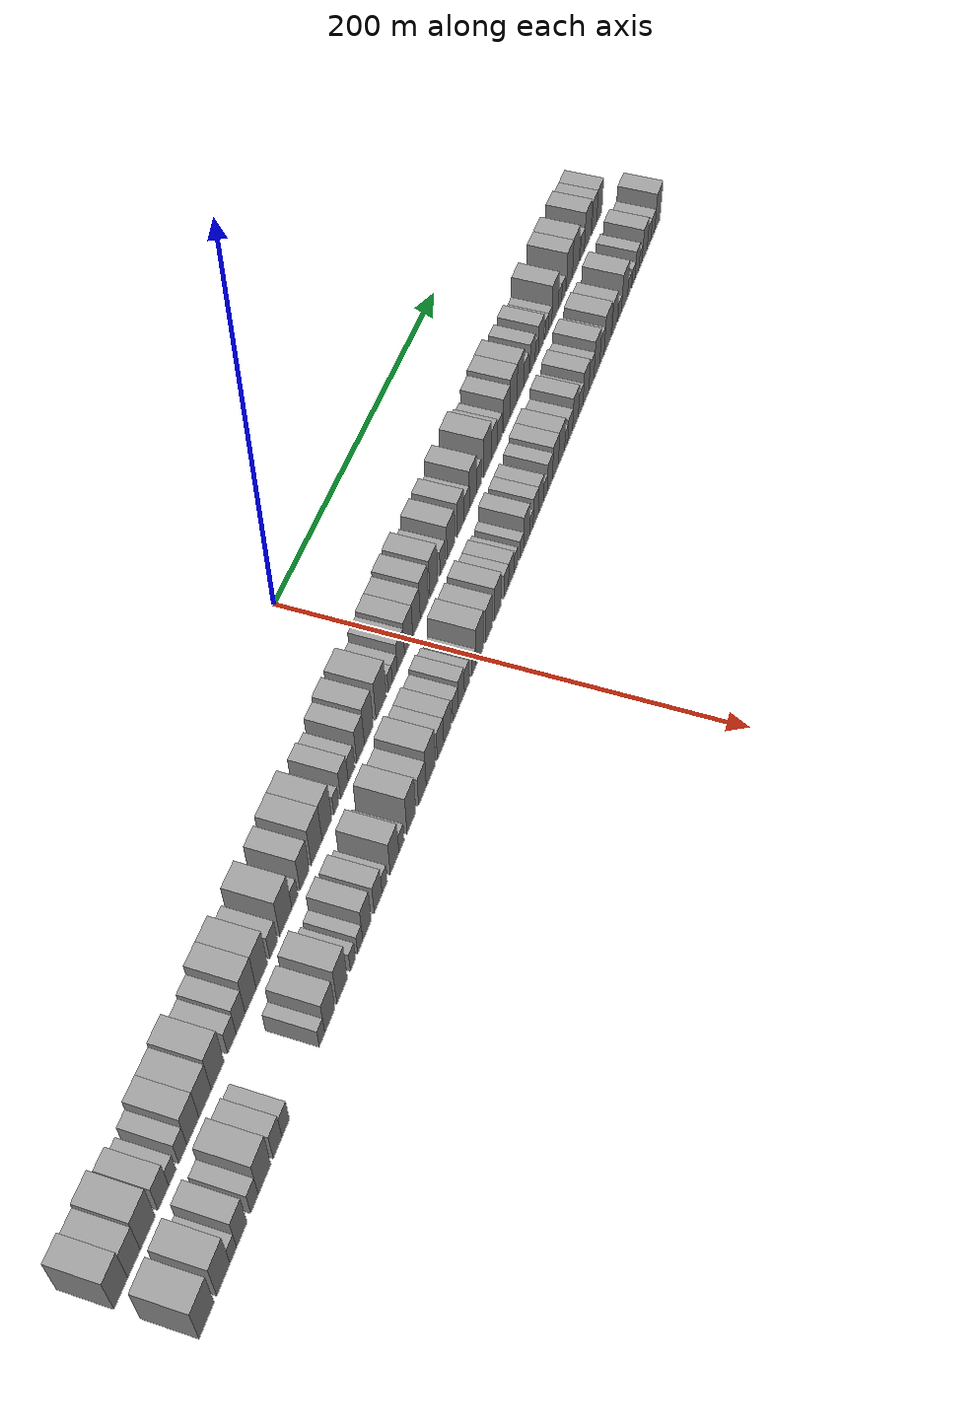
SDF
<sdf version="1.6">
 <world name="default">
  <scene>
   <sky><clouds><speed>12</speed></clouds></sky>
   <ambient>0.4 0.4 0.4 1</ambient>
   <background>0.7 0.7 0.7 1</background>
   <shadows>1</shadows>
  </scene>
  <gravity>0 0 -9.8066</gravity>
  <magnetic_field>6e-06 2.3e-05 -4.2e-05</magnetic_field>
  <physics default="0" name="default_physics" type="ode">
   <ode>
    <solver>
     <type>quick</type>
     <iters>10</iters>
     <sor>1.0</sor>
     <use_dynamic_moi_rescaling>0</use_dynamic_moi_rescaling>
    </solver>
    <constraints>
     <cfm>0</cfm>
     <erp>0.2</erp>
     <contact_max_correcting_vel>100</contact_max_correcting_vel>
     <contact_surface_layer>0.001</contact_surface_layer>
    </constraints>
   </ode>
   <max_step_size>0.004</max_step_size>
   <real_time_factor>1</real_time_factor>
   <real_time_update_rate>250</real_time_update_rate>
  </physics>
  <light name="sun" type="directional">
   <pose>0 0 10 0 0 0</pose>
   <diffuse>0.8 0.8 0.8 1</diffuse>
   <specular>0.2 0.2 0.2 1</specular>
   <attenuation>
    <range>1000</range>
    <constant>0.9</constant>
    <linear>0.01</linear>
    <quadratic>0.001</quadratic>
   </attenuation>
   <direction>-0.5 0.1 -0.9</direction>
  </light>
  <model name="building_1">
   <static>1</static>
   <pose>50.0000 -272.9200 0 0.000000 0.000000 0.000000</pose>
   <link name="link">
    <pose>0 0 12.00 0 0 0</pose>
    <collision name="collision"><geometry><box><size>20.0000 10.1599 24.0000</size></box></geometry></collision>
    <visual name="visual">
     <cast_shadows>0</cast_shadows>
     <geometry><box><size>20.0000 10.1599 24.0000</size></box></geometry>
     <material>
      <script>
       <uri>model://grey_wall/materials/scripts</uri>
       <uri>model://grey_wall/materials/textures</uri>
       <name>vrc/grey_wall</name>
      </script>
     </material>
    </visual>
   </link>
  </model>
  <model name="building_2">
   <static>1</static>
   <pose>50.0000 -263.1600 0 0.000000 0.000000 0.000000</pose>
   <link name="link">
    <pose>0 0 10.50 0 0 0</pose>
    <collision name="collision"><geometry><box><size>20.0000 9.3602 21.0000</size></box></geometry></collision>
    <visual name="visual">
     <cast_shadows>0</cast_shadows>
     <geometry><box><size>20.0000 9.3602 21.0000</size></box></geometry>
     <material>
      <script>
       <uri>model://grey_wall/materials/scripts</uri>
       <uri>model://grey_wall/materials/textures</uri>
       <name>vrc/grey_wall</name>
      </script>
     </material>
    </visual>
   </link>
  </model>
  <model name="building_3">
   <static>1</static>
   <pose>50.0000 -252.7871 0 0.000000 0.000000 0.000000</pose>
   <link name="link">
    <pose>0 0 12.00 0 0 0</pose>
    <collision name="collision"><geometry><box><size>20.0000 11.3856 24.0000</size></box></geometry></collision>
    <visual name="visual">
     <cast_shadows>0</cast_shadows>
     <geometry><box><size>20.0000 11.3856 24.0000</size></box></geometry>
     <material>
      <script>
       <uri>model://grey_wall/materials/scripts</uri>
       <uri>model://grey_wall/materials/textures</uri>
       <name>vrc/grey_wall</name>
      </script>
     </material>
    </visual>
   </link>
  </model>
  <model name="building_4">
   <static>1</static>
   <pose>50.0000 -240.8640 0 0.000000 0.000000 0.000000</pose>
   <link name="link">
    <pose>0 0 9.00 0 0 0</pose>
    <collision name="collision"><geometry><box><size>20.0000 8.4605 18.0000</size></box></geometry></collision>
    <visual name="visual">
     <cast_shadows>0</cast_shadows>
     <geometry><box><size>20.0000 8.4605 18.0000</size></box></geometry>
     <material>
      <script>
       <uri>model://grey_wall/materials/scripts</uri>
       <uri>model://grey_wall/materials/textures</uri>
       <name>vrc/grey_wall</name>
      </script>
     </material>
    </visual>
   </link>
  </model>
  <model name="building_5">
   <static>1</static>
   <pose>50.0000 -233.6953 0 0.000000 0.000000 0.000000</pose>
   <link name="link">
    <pose>0 0 6.00 0 0 0</pose>
    <collision name="collision"><geometry><box><size>20.0000 5.8770 12.0000</size></box></geometry></collision>
    <visual name="visual">
     <cast_shadows>0</cast_shadows>
     <geometry><box><size>20.0000 5.8770 12.0000</size></box></geometry>
     <material>
      <script>
       <uri>model://grey_wall/materials/scripts</uri>
       <uri>model://grey_wall/materials/textures</uri>
       <name>vrc/grey_wall</name>
      </script>
     </material>
    </visual>
   </link>
  </model>
  <model name="building_6">
   <static>1</static>
   <pose>50.0000 -225.4794 0 0.000000 0.000000 0.000000</pose>
   <link name="link">
    <pose>0 0 7.50 0 0 0</pose>
    <collision name="collision"><geometry><box><size>20.0000 6.5549 15.0000</size></box></geometry></collision>
    <visual name="visual">
     <cast_shadows>0</cast_shadows>
     <geometry><box><size>20.0000 6.5549 15.0000</size></box></geometry>
     <material>
      <script>
       <uri>model://grey_wall/materials/scripts</uri>
       <uri>model://grey_wall/materials/textures</uri>
       <name>vrc/grey_wall</name>
      </script>
     </material>
    </visual>
   </link>
  </model>
  <model name="building_7">
   <static>1</static>
   <pose>50.0000 -217.2844 0 0.000000 0.000000 0.000000</pose>
   <link name="link">
    <pose>0 0 10.50 0 0 0</pose>
    <collision name="collision"><geometry><box><size>20.0000 9.8351 21.0000</size></box></geometry></collision>
    <visual name="visual">
     <cast_shadows>0</cast_shadows>
     <geometry><box><size>20.0000 9.8351 21.0000</size></box></geometry>
     <material>
      <script>
       <uri>model://grey_wall/materials/scripts</uri>
       <uri>model://grey_wall/materials/textures</uri>
       <name>vrc/grey_wall</name>
      </script>
     </material>
    </visual>
   </link>
  </model>
  <model name="building_8">
   <static>1</static>
   <pose>50.0000 -207.2221 0 0.000000 0.000000 0.000000</pose>
   <link name="link">
    <pose>0 0 10.50 0 0 0</pose>
    <collision name="collision"><geometry><box><size>20.0000 10.2895 21.0000</size></box></geometry></collision>
    <visual name="visual">
     <cast_shadows>0</cast_shadows>
     <geometry><box><size>20.0000 10.2895 21.0000</size></box></geometry>
     <material>
      <script>
       <uri>model://grey_wall/materials/scripts</uri>
       <uri>model://grey_wall/materials/textures</uri>
       <name>vrc/grey_wall</name>
      </script>
     </material>
    </visual>
   </link>
  </model>
  <model name="building_9">
   <static>1</static>
   <pose>50.0000 -196.6177 0 0.000000 0.000000 0.000000</pose>
   <link name="link">
    <pose>0 0 12.00 0 0 0</pose>
    <collision name="collision"><geometry><box><size>20.0000 10.9194 24.0000</size></box></geometry></collision>
    <visual name="visual">
     <cast_shadows>0</cast_shadows>
     <geometry><box><size>20.0000 10.9194 24.0000</size></box></geometry>
     <material>
      <script>
       <uri>model://grey_wall/materials/scripts</uri>
       <uri>model://grey_wall/materials/textures</uri>
       <name>vrc/grey_wall</name>
      </script>
     </material>
    </visual>
   </link>
  </model>
  <model name="building_10">
   <static>1</static>
   <pose>50.0000 -184.4147 0 0.000000 0.000000 0.000000</pose>
   <link name="link">
    <pose>0 0 7.50 0 0 0</pose>
    <collision name="collision"><geometry><box><size>20.0000 7.4866 15.0000</size></box></geometry></collision>
    <visual name="visual">
     <cast_shadows>0</cast_shadows>
     <geometry><box><size>20.0000 7.4866 15.0000</size></box></geometry>
     <material>
      <script>
       <uri>model://grey_wall/materials/scripts</uri>
       <uri>model://grey_wall/materials/textures</uri>
       <name>vrc/grey_wall</name>
      </script>
     </material>
    </visual>
   </link>
  </model>
  <model name="building_11">
   <static>1</static>
   <pose>50.0000 -176.6504 0 0.000000 0.000000 0.000000</pose>
   <link name="link">
    <pose>0 0 9.00 0 0 0</pose>
    <collision name="collision"><geometry><box><size>20.0000 8.0421 18.0000</size></box></geometry></collision>
    <visual name="visual">
     <cast_shadows>0</cast_shadows>
     <geometry><box><size>20.0000 8.0421 18.0000</size></box></geometry>
     <material>
      <script>
       <uri>model://grey_wall/materials/scripts</uri>
       <uri>model://grey_wall/materials/textures</uri>
       <name>vrc/grey_wall</name>
      </script>
     </material>
    </visual>
   </link>
  </model>
  <model name="building_12">
   <static>1</static>
   <pose>50.0000 -167.6863 0 0.000000 0.000000 0.000000</pose>
   <link name="link">
    <pose>0 0 12.00 0 0 0</pose>
    <collision name="collision"><geometry><box><size>20.0000 9.8860 24.0000</size></box></geometry></collision>
    <visual name="visual">
     <cast_shadows>0</cast_shadows>
     <geometry><box><size>20.0000 9.8860 24.0000</size></box></geometry>
     <material>
      <script>
       <uri>model://grey_wall/materials/scripts</uri>
       <uri>model://grey_wall/materials/textures</uri>
       <name>vrc/grey_wall</name>
      </script>
     </material>
    </visual>
   </link>
  </model>
  <model name="building_13">
   <static>1</static>
   <pose>50.0000 -157.5218 0 0.000000 0.000000 0.000000</pose>
   <link name="link">
    <pose>0 0 12.00 0 0 0</pose>
    <collision name="collision"><geometry><box><size>20.0000 10.4430 24.0000</size></box></geometry></collision>
    <visual name="visual">
     <cast_shadows>0</cast_shadows>
     <geometry><box><size>20.0000 10.4430 24.0000</size></box></geometry>
     <material>
      <script>
       <uri>model://grey_wall/materials/scripts</uri>
       <uri>model://grey_wall/materials/textures</uri>
       <name>vrc/grey_wall</name>
      </script>
     </material>
    </visual>
   </link>
  </model>
  <model name="building_14">
   <static>1</static>
   <pose>50.0000 -146.6202 0 0.000000 0.000000 0.000000</pose>
   <link name="link">
    <pose>0 0 7.50 0 0 0</pose>
    <collision name="collision"><geometry><box><size>20.0000 7.3601 15.0000</size></box></geometry></collision>
    <visual name="visual">
     <cast_shadows>0</cast_shadows>
     <geometry><box><size>20.0000 7.3601 15.0000</size></box></geometry>
     <material>
      <script>
       <uri>model://grey_wall/materials/scripts</uri>
       <uri>model://grey_wall/materials/textures</uri>
       <name>vrc/grey_wall</name>
      </script>
     </material>
    </visual>
   </link>
  </model>
  <model name="building_15">
   <static>1</static>
   <pose>50.0000 -135.1217 0 0.000000 0.000000 0.000000</pose>
   <link name="link">
    <pose>0 0 12.00 0 0 0</pose>
    <collision name="collision"><geometry><box><size>20.0000 11.6370 24.0000</size></box></geometry></collision>
    <visual name="visual">
     <cast_shadows>0</cast_shadows>
     <geometry><box><size>20.0000 11.6370 24.0000</size></box></geometry>
     <material>
      <script>
       <uri>model://grey_wall/materials/scripts</uri>
       <uri>model://grey_wall/materials/textures</uri>
       <name>vrc/grey_wall</name>
      </script>
     </material>
    </visual>
   </link>
  </model>
  <model name="building_16">
   <static>1</static>
   <pose>50.0000 -126.3583 0 0.000000 0.000000 0.000000</pose>
   <link name="link">
    <pose>0 0 6.00 0 0 0</pose>
    <collision name="collision"><geometry><box><size>20.0000 5.8898 12.0000</size></box></geometry></collision>
    <visual name="visual">
     <cast_shadows>0</cast_shadows>
     <geometry><box><size>20.0000 5.8898 12.0000</size></box></geometry>
     <material>
      <script>
       <uri>model://grey_wall/materials/scripts</uri>
       <uri>model://grey_wall/materials/textures</uri>
       <name>vrc/grey_wall</name>
      </script>
     </material>
    </visual>
   </link>
  </model>
  <model name="building_17">
   <static>1</static>
   <pose>50.0000 -116.8223 0 0.000000 0.000000 0.000000</pose>
   <link name="link">
    <pose>0 0 10.50 0 0 0</pose>
    <collision name="collision"><geometry><box><size>20.0000 9.1821 21.0000</size></box></geometry></collision>
    <visual name="visual">
     <cast_shadows>0</cast_shadows>
     <geometry><box><size>20.0000 9.1821 21.0000</size></box></geometry>
     <material>
      <script>
       <uri>model://grey_wall/materials/scripts</uri>
       <uri>model://grey_wall/materials/textures</uri>
       <name>vrc/grey_wall</name>
      </script>
     </material>
    </visual>
   </link>
  </model>
  <model name="building_18">
   <static>1</static>
   <pose>50.0000 -104.7328 0 0.000000 0.000000 0.000000</pose>
   <link name="link">
    <pose>0 0 12.00 0 0 0</pose>
    <collision name="collision"><geometry><box><size>20.0000 10.9970 24.0000</size></box></geometry></collision>
    <visual name="visual">
     <cast_shadows>0</cast_shadows>
     <geometry><box><size>20.0000 10.9970 24.0000</size></box></geometry>
     <material>
      <script>
       <uri>model://grey_wall/materials/scripts</uri>
       <uri>model://grey_wall/materials/textures</uri>
       <name>vrc/grey_wall</name>
      </script>
     </material>
    </visual>
   </link>
  </model>
  <model name="building_19">
   <static>1</static>
   <pose>50.0000 -94.2725 0 0.000000 0.000000 0.000000</pose>
   <link name="link">
    <pose>0 0 12.00 0 0 0</pose>
    <collision name="collision"><geometry><box><size>20.0000 9.9236 24.0000</size></box></geometry></collision>
    <visual name="visual">
     <cast_shadows>0</cast_shadows>
     <geometry><box><size>20.0000 9.9236 24.0000</size></box></geometry>
     <material>
      <script>
       <uri>model://grey_wall/materials/scripts</uri>
       <uri>model://grey_wall/materials/textures</uri>
       <name>vrc/grey_wall</name>
      </script>
     </material>
    </visual>
   </link>
  </model>
  <model name="building_20">
   <static>1</static>
   <pose>50.0000 -84.7162 0 0.000000 0.000000 0.000000</pose>
   <link name="link">
    <pose>0 0 6.00 0 0 0</pose>
    <collision name="collision"><geometry><box><size>20.0000 5.1888 12.0000</size></box></geometry></collision>
    <visual name="visual">
     <cast_shadows>0</cast_shadows>
     <geometry><box><size>20.0000 5.1888 12.0000</size></box></geometry>
     <material>
      <script>
       <uri>model://grey_wall/materials/scripts</uri>
       <uri>model://grey_wall/materials/textures</uri>
       <name>vrc/grey_wall</name>
      </script>
     </material>
    </visual>
   </link>
  </model>
  <model name="building_21">
   <static>1</static>
   <pose>50.0000 -76.0519 0 0.000000 0.000000 0.000000</pose>
   <link name="link">
    <pose>0 0 9.00 0 0 0</pose>
    <collision name="collision"><geometry><box><size>20.0000 8.1398 18.0000</size></box></geometry></collision>
    <visual name="visual">
     <cast_shadows>0</cast_shadows>
     <geometry><box><size>20.0000 8.1398 18.0000</size></box></geometry>
     <material>
      <script>
       <uri>model://grey_wall/materials/scripts</uri>
       <uri>model://grey_wall/materials/textures</uri>
       <name>vrc/grey_wall</name>
      </script>
     </material>
    </visual>
   </link>
  </model>
  <model name="building_22">
   <static>1</static>
   <pose>50.0000 -68.4234 0 0.000000 0.000000 0.000000</pose>
   <link name="link">
    <pose>0 0 7.50 0 0 0</pose>
    <collision name="collision"><geometry><box><size>20.0000 7.1172 15.0000</size></box></geometry></collision>
    <visual name="visual">
     <cast_shadows>0</cast_shadows>
     <geometry><box><size>20.0000 7.1172 15.0000</size></box></geometry>
     <material>
      <script>
       <uri>model://grey_wall/materials/scripts</uri>
       <uri>model://grey_wall/materials/textures</uri>
       <name>vrc/grey_wall</name>
      </script>
     </material>
    </visual>
   </link>
  </model>
  <model name="building_23">
   <static>1</static>
   <pose>50.0000 -58.6308 0 0.000000 0.000000 0.000000</pose>
   <link name="link">
    <pose>0 0 10.50 0 0 0</pose>
    <collision name="collision"><geometry><box><size>20.0000 8.4679 21.0000</size></box></geometry></collision>
    <visual name="visual">
     <cast_shadows>0</cast_shadows>
     <geometry><box><size>20.0000 8.4679 21.0000</size></box></geometry>
     <material>
      <script>
       <uri>model://grey_wall/materials/scripts</uri>
       <uri>model://grey_wall/materials/textures</uri>
       <name>vrc/grey_wall</name>
      </script>
     </material>
    </visual>
   </link>
  </model>
  <model name="building_24">
   <static>1</static>
   <pose>50.0000 -49.4877 0 0.000000 0.000000 0.000000</pose>
   <link name="link">
    <pose>0 0 12.00 0 0 0</pose>
    <collision name="collision"><geometry><box><size>20.0000 9.8183 24.0000</size></box></geometry></collision>
    <visual name="visual">
     <cast_shadows>0</cast_shadows>
     <geometry><box><size>20.0000 9.8183 24.0000</size></box></geometry>
     <material>
      <script>
       <uri>model://grey_wall/materials/scripts</uri>
       <uri>model://grey_wall/materials/textures</uri>
       <name>vrc/grey_wall</name>
      </script>
     </material>
    </visual>
   </link>
  </model>
  <model name="building_25">
   <static>1</static>
   <pose>50.0000 -35.6482 0 0.000000 0.000000 0.000000</pose>
   <link name="link">
    <pose>0 0 12.00 0 0 0</pose>
    <collision name="collision"><geometry><box><size>20.0000 11.8606 24.0000</size></box></geometry></collision>
    <visual name="visual">
     <cast_shadows>0</cast_shadows>
     <geometry><box><size>20.0000 11.8606 24.0000</size></box></geometry>
     <material>
      <script>
       <uri>model://grey_wall/materials/scripts</uri>
       <uri>model://grey_wall/materials/textures</uri>
       <name>vrc/grey_wall</name>
      </script>
     </material>
    </visual>
   </link>
  </model>
  <model name="building_26">
   <static>1</static>
   <pose>50.0000 -25.2976 0 0.000000 0.000000 0.000000</pose>
   <link name="link">
    <pose>0 0 6.00 0 0 0</pose>
    <collision name="collision"><geometry><box><size>20.0000 4.8406 12.0000</size></box></geometry></collision>
    <visual name="visual">
     <cast_shadows>0</cast_shadows>
     <geometry><box><size>20.0000 4.8406 12.0000</size></box></geometry>
     <material>
      <script>
       <uri>model://grey_wall/materials/scripts</uri>
       <uri>model://grey_wall/materials/textures</uri>
       <name>vrc/grey_wall</name>
      </script>
     </material>
    </visual>
   </link>
  </model>
  <model name="building_27">
   <static>1</static>
   <pose>50.0000 -20.0082 0 0.000000 0.000000 0.000000</pose>
   <link name="link">
    <pose>0 0 6.00 0 0 0</pose>
    <collision name="collision"><geometry><box><size>20.0000 5.7383 12.0000</size></box></geometry></collision>
    <visual name="visual">
     <cast_shadows>0</cast_shadows>
     <geometry><box><size>20.0000 5.7383 12.0000</size></box></geometry>
     <material>
      <script>
       <uri>model://grey_wall/materials/scripts</uri>
       <uri>model://grey_wall/materials/textures</uri>
       <name>vrc/grey_wall</name>
      </script>
     </material>
    </visual>
   </link>
  </model>
  <model name="building_28">
   <static>1</static>
   <pose>50.0000 -12.7895 0 0.000000 0.000000 0.000000</pose>
   <link name="link">
    <pose>0 0 9.00 0 0 0</pose>
    <collision name="collision"><geometry><box><size>20.0000 8.6990 18.0000</size></box></geometry></collision>
    <visual name="visual">
     <cast_shadows>0</cast_shadows>
     <geometry><box><size>20.0000 8.6990 18.0000</size></box></geometry>
     <material>
      <script>
       <uri>model://grey_wall/materials/scripts</uri>
       <uri>model://grey_wall/materials/textures</uri>
       <name>vrc/grey_wall</name>
      </script>
     </material>
    </visual>
   </link>
  </model>
  <model name="building_29">
   <static>1</static>
   <pose>50.0000 -3.5440 0 0.000000 0.000000 0.000000</pose>
   <link name="link">
    <pose>0 0 10.50 0 0 0</pose>
    <collision name="collision"><geometry><box><size>20.0000 9.7920 21.0000</size></box></geometry></collision>
    <visual name="visual">
     <cast_shadows>0</cast_shadows>
     <geometry><box><size>20.0000 9.7920 21.0000</size></box></geometry>
     <material>
      <script>
       <uri>model://grey_wall/materials/scripts</uri>
       <uri>model://grey_wall/materials/textures</uri>
       <name>vrc/grey_wall</name>
      </script>
     </material>
    </visual>
   </link>
  </model>
  <model name="building_30">
   <static>1</static>
   <pose>50.0000 5.9721 0 0.000000 0.000000 0.000000</pose>
   <link name="link">
    <pose>0 0 10.50 0 0 0</pose>
    <collision name="collision"><geometry><box><size>20.0000 9.2402 21.0000</size></box></geometry></collision>
    <visual name="visual">
     <cast_shadows>0</cast_shadows>
     <geometry><box><size>20.0000 9.2402 21.0000</size></box></geometry>
     <material>
      <script>
       <uri>model://grey_wall/materials/scripts</uri>
       <uri>model://grey_wall/materials/textures</uri>
       <name>vrc/grey_wall</name>
      </script>
     </material>
    </visual>
   </link>
  </model>
  <model name="building_31">
   <static>1</static>
   <pose>50.0000 15.5483 0 0.000000 0.000000 0.000000</pose>
   <link name="link">
    <pose>0 0 12.00 0 0 0</pose>
    <collision name="collision"><geometry><box><size>20.0000 9.9122 24.0000</size></box></geometry></collision>
    <visual name="visual">
     <cast_shadows>0</cast_shadows>
     <geometry><box><size>20.0000 9.9122 24.0000</size></box></geometry>
     <material>
      <script>
       <uri>model://grey_wall/materials/scripts</uri>
       <uri>model://grey_wall/materials/textures</uri>
       <name>vrc/grey_wall</name>
      </script>
     </material>
    </visual>
   </link>
  </model>
  <model name="building_32">
   <static>1</static>
   <pose>50.0000 27.4965 0 0.000000 0.000000 0.000000</pose>
   <link name="link">
    <pose>0 0 12.00 0 0 0</pose>
    <collision name="collision"><geometry><box><size>20.0000 9.9842 24.0000</size></box></geometry></collision>
    <visual name="visual">
     <cast_shadows>0</cast_shadows>
     <geometry><box><size>20.0000 9.9842 24.0000</size></box></geometry>
     <material>
      <script>
       <uri>model://grey_wall/materials/scripts</uri>
       <uri>model://grey_wall/materials/textures</uri>
       <name>vrc/grey_wall</name>
      </script>
     </material>
    </visual>
   </link>
  </model>
  <model name="building_33">
   <static>1</static>
   <pose>50.0000 38.9702 0 0.000000 0.000000 0.000000</pose>
   <link name="link">
    <pose>0 0 7.50 0 0 0</pose>
    <collision name="collision"><geometry><box><size>20.0000 6.9632 15.0000</size></box></geometry></collision>
    <visual name="visual">
     <cast_shadows>0</cast_shadows>
     <geometry><box><size>20.0000 6.9632 15.0000</size></box></geometry>
     <material>
      <script>
       <uri>model://grey_wall/materials/scripts</uri>
       <uri>model://grey_wall/materials/textures</uri>
       <name>vrc/grey_wall</name>
      </script>
     </material>
    </visual>
   </link>
  </model>
  <model name="building_34">
   <static>1</static>
   <pose>50.0000 49.6491 0 0.000000 0.000000 0.000000</pose>
   <link name="link">
    <pose>0 0 10.50 0 0 0</pose>
    <collision name="collision"><geometry><box><size>20.0000 10.3947 21.0000</size></box></geometry></collision>
    <visual name="visual">
     <cast_shadows>0</cast_shadows>
     <geometry><box><size>20.0000 10.3947 21.0000</size></box></geometry>
     <material>
      <script>
       <uri>model://grey_wall/materials/scripts</uri>
       <uri>model://grey_wall/materials/textures</uri>
       <name>vrc/grey_wall</name>
      </script>
     </material>
    </visual>
   </link>
  </model>
  <model name="building_35">
   <static>1</static>
   <pose>50.0000 62.3072 0 0.000000 0.000000 0.000000</pose>
   <link name="link">
    <pose>0 0 10.50 0 0 0</pose>
    <collision name="collision"><geometry><box><size>20.0000 8.9213 21.0000</size></box></geometry></collision>
    <visual name="visual">
     <cast_shadows>0</cast_shadows>
     <geometry><box><size>20.0000 8.9213 21.0000</size></box></geometry>
     <material>
      <script>
       <uri>model://grey_wall/materials/scripts</uri>
       <uri>model://grey_wall/materials/textures</uri>
       <name>vrc/grey_wall</name>
      </script>
     </material>
    </visual>
   </link>
  </model>
  <model name="building_36">
   <static>1</static>
   <pose>50.0000 70.4754 0 0.000000 0.000000 0.000000</pose>
   <link name="link">
    <pose>0 0 7.50 0 0 0</pose>
    <collision name="collision"><geometry><box><size>20.0000 7.4153 15.0000</size></box></geometry></collision>
    <visual name="visual">
     <cast_shadows>0</cast_shadows>
     <geometry><box><size>20.0000 7.4153 15.0000</size></box></geometry>
     <material>
      <script>
       <uri>model://grey_wall/materials/scripts</uri>
       <uri>model://grey_wall/materials/textures</uri>
       <name>vrc/grey_wall</name>
      </script>
     </material>
    </visual>
   </link>
  </model>
  <model name="building_37">
   <static>1</static>
   <pose>50.0000 79.1271 0 0.000000 0.000000 0.000000</pose>
   <link name="link">
    <pose>0 0 12.00 0 0 0</pose>
    <collision name="collision"><geometry><box><size>20.0000 9.8882 24.0000</size></box></geometry></collision>
    <visual name="visual">
     <cast_shadows>0</cast_shadows>
     <geometry><box><size>20.0000 9.8882 24.0000</size></box></geometry>
     <material>
      <script>
       <uri>model://grey_wall/materials/scripts</uri>
       <uri>model://grey_wall/materials/textures</uri>
       <name>vrc/grey_wall</name>
      </script>
     </material>
    </visual>
   </link>
  </model>
  <model name="building_38">
   <static>1</static>
   <pose>50.0000 87.3557 0 0.000000 0.000000 0.000000</pose>
   <link name="link">
    <pose>0 0 7.50 0 0 0</pose>
    <collision name="collision"><geometry><box><size>20.0000 6.5690 15.0000</size></box></geometry></collision>
    <visual name="visual">
     <cast_shadows>0</cast_shadows>
     <geometry><box><size>20.0000 6.5690 15.0000</size></box></geometry>
     <material>
      <script>
       <uri>model://grey_wall/materials/scripts</uri>
       <uri>model://grey_wall/materials/textures</uri>
       <name>vrc/grey_wall</name>
      </script>
     </material>
    </visual>
   </link>
  </model>
  <model name="building_39">
   <static>1</static>
   <pose>50.0000 99.4157 0 0.000000 0.000000 0.000000</pose>
   <link name="link">
    <pose>0 0 12.00 0 0 0</pose>
    <collision name="collision"><geometry><box><size>20.0000 11.5509 24.0000</size></box></geometry></collision>
    <visual name="visual">
     <cast_shadows>0</cast_shadows>
     <geometry><box><size>20.0000 11.5509 24.0000</size></box></geometry>
     <material>
      <script>
       <uri>model://grey_wall/materials/scripts</uri>
       <uri>model://grey_wall/materials/textures</uri>
       <name>vrc/grey_wall</name>
      </script>
     </material>
    </visual>
   </link>
  </model>
  <model name="building_40">
   <static>1</static>
   <pose>50.0000 109.0097 0 0.000000 0.000000 0.000000</pose>
   <link name="link">
    <pose>0 0 9.00 0 0 0</pose>
    <collision name="collision"><geometry><box><size>20.0000 7.6370 18.0000</size></box></geometry></collision>
    <visual name="visual">
     <cast_shadows>0</cast_shadows>
     <geometry><box><size>20.0000 7.6370 18.0000</size></box></geometry>
     <material>
      <script>
       <uri>model://grey_wall/materials/scripts</uri>
       <uri>model://grey_wall/materials/textures</uri>
       <name>vrc/grey_wall</name>
      </script>
     </material>
    </visual>
   </link>
  </model>
  <model name="building_41">
   <static>1</static>
   <pose>50.0000 116.3840 0 0.000000 0.000000 0.000000</pose>
   <link name="link">
    <pose>0 0 7.50 0 0 0</pose>
    <collision name="collision"><geometry><box><size>20.0000 7.1115 15.0000</size></box></geometry></collision>
    <visual name="visual">
     <cast_shadows>0</cast_shadows>
     <geometry><box><size>20.0000 7.1115 15.0000</size></box></geometry>
     <material>
      <script>
       <uri>model://grey_wall/materials/scripts</uri>
       <uri>model://grey_wall/materials/textures</uri>
       <name>vrc/grey_wall</name>
      </script>
     </material>
    </visual>
   </link>
  </model>
  <model name="building_42">
   <static>1</static>
   <pose>50.0000 126.7651 0 0.000000 0.000000 0.000000</pose>
   <link name="link">
    <pose>0 0 10.50 0 0 0</pose>
    <collision name="collision"><geometry><box><size>20.0000 9.6506 21.0000</size></box></geometry></collision>
    <visual name="visual">
     <cast_shadows>0</cast_shadows>
     <geometry><box><size>20.0000 9.6506 21.0000</size></box></geometry>
     <material>
      <script>
       <uri>model://grey_wall/materials/scripts</uri>
       <uri>model://grey_wall/materials/textures</uri>
       <name>vrc/grey_wall</name>
      </script>
     </material>
    </visual>
   </link>
  </model>
  <model name="building_43">
   <static>1</static>
   <pose>50.0000 136.8719 0 0.000000 0.000000 0.000000</pose>
   <link name="link">
    <pose>0 0 12.00 0 0 0</pose>
    <collision name="collision"><geometry><box><size>20.0000 10.5631 24.0000</size></box></geometry></collision>
    <visual name="visual">
     <cast_shadows>0</cast_shadows>
     <geometry><box><size>20.0000 10.5631 24.0000</size></box></geometry>
     <material>
      <script>
       <uri>model://grey_wall/materials/scripts</uri>
       <uri>model://grey_wall/materials/textures</uri>
       <name>vrc/grey_wall</name>
      </script>
     </material>
    </visual>
   </link>
  </model>
  <model name="building_44">
   <static>1</static>
   <pose>50.0000 147.2639 0 0.000000 0.000000 0.000000</pose>
   <link name="link">
    <pose>0 0 12.00 0 0 0</pose>
    <collision name="collision"><geometry><box><size>20.0000 10.2209 24.0000</size></box></geometry></collision>
    <visual name="visual">
     <cast_shadows>0</cast_shadows>
     <geometry><box><size>20.0000 10.2209 24.0000</size></box></geometry>
     <material>
      <script>
       <uri>model://grey_wall/materials/scripts</uri>
       <uri>model://grey_wall/materials/textures</uri>
       <name>vrc/grey_wall</name>
      </script>
     </material>
    </visual>
   </link>
  </model>
  <model name="building_45">
   <static>1</static>
   <pose>50.0000 156.0411 0 0.000000 0.000000 0.000000</pose>
   <link name="link">
    <pose>0 0 7.50 0 0 0</pose>
    <collision name="collision"><geometry><box><size>20.0000 7.3334 15.0000</size></box></geometry></collision>
    <visual name="visual">
     <cast_shadows>0</cast_shadows>
     <geometry><box><size>20.0000 7.3334 15.0000</size></box></geometry>
     <material>
      <script>
       <uri>model://grey_wall/materials/scripts</uri>
       <uri>model://grey_wall/materials/textures</uri>
       <name>vrc/grey_wall</name>
      </script>
     </material>
    </visual>
   </link>
  </model>
  <model name="building_46">
   <static>1</static>
   <pose>50.0000 165.6689 0 0.000000 0.000000 0.000000</pose>
   <link name="link">
    <pose>0 0 9.00 0 0 0</pose>
    <collision name="collision"><geometry><box><size>20.0000 7.9223 18.0000</size></box></geometry></collision>
    <visual name="visual">
     <cast_shadows>0</cast_shadows>
     <geometry><box><size>20.0000 7.9223 18.0000</size></box></geometry>
     <material>
      <script>
       <uri>model://grey_wall/materials/scripts</uri>
       <uri>model://grey_wall/materials/textures</uri>
       <name>vrc/grey_wall</name>
      </script>
     </material>
    </visual>
   </link>
  </model>
  <model name="building_47">
   <static>1</static>
   <pose>50.0000 172.1185 0 0.000000 0.000000 0.000000</pose>
   <link name="link">
    <pose>0 0 6.00 0 0 0</pose>
    <collision name="collision"><geometry><box><size>20.0000 4.9769 12.0000</size></box></geometry></collision>
    <visual name="visual">
     <cast_shadows>0</cast_shadows>
     <geometry><box><size>20.0000 4.9769 12.0000</size></box></geometry>
     <material>
      <script>
       <uri>model://grey_wall/materials/scripts</uri>
       <uri>model://grey_wall/materials/textures</uri>
       <name>vrc/grey_wall</name>
      </script>
     </material>
    </visual>
   </link>
  </model>
  <model name="building_48">
   <static>1</static>
   <pose>50.0000 178.9828 0 0.000000 0.000000 0.000000</pose>
   <link name="link">
    <pose>0 0 9.00 0 0 0</pose>
    <collision name="collision"><geometry><box><size>20.0000 8.7516 18.0000</size></box></geometry></collision>
    <visual name="visual">
     <cast_shadows>0</cast_shadows>
     <geometry><box><size>20.0000 8.7516 18.0000</size></box></geometry>
     <material>
      <script>
       <uri>model://grey_wall/materials/scripts</uri>
       <uri>model://grey_wall/materials/textures</uri>
       <name>vrc/grey_wall</name>
      </script>
     </material>
    </visual>
   </link>
  </model>
  <model name="building_49">
   <static>1</static>
   <pose>50.0000 188.1513 0 0.000000 0.000000 0.000000</pose>
   <link name="link">
    <pose>0 0 6.00 0 0 0</pose>
    <collision name="collision"><geometry><box><size>20.0000 5.5853 12.0000</size></box></geometry></collision>
    <visual name="visual">
     <cast_shadows>0</cast_shadows>
     <geometry><box><size>20.0000 5.5853 12.0000</size></box></geometry>
     <material>
      <script>
       <uri>model://grey_wall/materials/scripts</uri>
       <uri>model://grey_wall/materials/textures</uri>
       <name>vrc/grey_wall</name>
      </script>
     </material>
    </visual>
   </link>
  </model>
  <model name="building_50">
   <static>1</static>
   <pose>50.0000 193.5602 0 0.000000 0.000000 0.000000</pose>
   <link name="link">
    <pose>0 0 6.00 0 0 0</pose>
    <collision name="collision"><geometry><box><size>20.0000 5.2325 12.0000</size></box></geometry></collision>
    <visual name="visual">
     <cast_shadows>0</cast_shadows>
     <geometry><box><size>20.0000 5.2325 12.0000</size></box></geometry>
     <material>
      <script>
       <uri>model://grey_wall/materials/scripts</uri>
       <uri>model://grey_wall/materials/textures</uri>
       <name>vrc/grey_wall</name>
      </script>
     </material>
    </visual>
   </link>
  </model>
  <model name="building_51">
   <static>1</static>
   <pose>50.0000 201.5715 0 0.000000 0.000000 0.000000</pose>
   <link name="link">
    <pose>0 0 12.00 0 0 0</pose>
    <collision name="collision"><geometry><box><size>20.0000 10.7901 24.0000</size></box></geometry></collision>
    <visual name="visual">
     <cast_shadows>0</cast_shadows>
     <geometry><box><size>20.0000 10.7901 24.0000</size></box></geometry>
     <material>
      <script>
       <uri>model://grey_wall/materials/scripts</uri>
       <uri>model://grey_wall/materials/textures</uri>
       <name>vrc/grey_wall</name>
      </script>
     </material>
    </visual>
   </link>
  </model>
  <model name="building_52">
   <static>1</static>
   <pose>50.0000 209.6448 0 0.000000 0.000000 0.000000</pose>
   <link name="link">
    <pose>0 0 6.00 0 0 0</pose>
    <collision name="collision"><geometry><box><size>20.0000 5.3565 12.0000</size></box></geometry></collision>
    <visual name="visual">
     <cast_shadows>0</cast_shadows>
     <geometry><box><size>20.0000 5.3565 12.0000</size></box></geometry>
     <material>
      <script>
       <uri>model://grey_wall/materials/scripts</uri>
       <uri>model://grey_wall/materials/textures</uri>
       <name>vrc/grey_wall</name>
      </script>
     </material>
    </visual>
   </link>
  </model>
  <model name="building_53">
   <static>1</static>
   <pose>50.0000 215.2984 0 0.000000 0.000000 0.000000</pose>
   <link name="link">
    <pose>0 0 6.00 0 0 0</pose>
    <collision name="collision"><geometry><box><size>20.0000 5.9508 12.0000</size></box></geometry></collision>
    <visual name="visual">
     <cast_shadows>0</cast_shadows>
     <geometry><box><size>20.0000 5.9508 12.0000</size></box></geometry>
     <material>
      <script>
       <uri>model://grey_wall/materials/scripts</uri>
       <uri>model://grey_wall/materials/textures</uri>
       <name>vrc/grey_wall</name>
      </script>
     </material>
    </visual>
   </link>
  </model>
  <model name="building_54">
   <static>1</static>
   <pose>50.0000 225.3693 0 0.000000 0.000000 0.000000</pose>
   <link name="link">
    <pose>0 0 12.00 0 0 0</pose>
    <collision name="collision"><geometry><box><size>20.0000 10.1909 24.0000</size></box></geometry></collision>
    <visual name="visual">
     <cast_shadows>0</cast_shadows>
     <geometry><box><size>20.0000 10.1909 24.0000</size></box></geometry>
     <material>
      <script>
       <uri>model://grey_wall/materials/scripts</uri>
       <uri>model://grey_wall/materials/textures</uri>
       <name>vrc/grey_wall</name>
      </script>
     </material>
    </visual>
   </link>
  </model>
  <model name="building_55">
   <static>1</static>
   <pose>50.0000 236.1086 0 0.000000 0.000000 0.000000</pose>
   <link name="link">
    <pose>0 0 12.00 0 0 0</pose>
    <collision name="collision"><geometry><box><size>20.0000 11.2876 24.0000</size></box></geometry></collision>
    <visual name="visual">
     <cast_shadows>0</cast_shadows>
     <geometry><box><size>20.0000 11.2876 24.0000</size></box></geometry>
     <material>
      <script>
       <uri>model://grey_wall/materials/scripts</uri>
       <uri>model://grey_wall/materials/textures</uri>
       <name>vrc/grey_wall</name>
      </script>
     </material>
    </visual>
   </link>
  </model>
  <model name="building_56">
   <static>1</static>
   <pose>50.0000 247.4181 0 0.000000 0.000000 0.000000</pose>
   <link name="link">
    <pose>0 0 7.50 0 0 0</pose>
    <collision name="collision"><geometry><box><size>20.0000 7.3316 15.0000</size></box></geometry></collision>
    <visual name="visual">
     <cast_shadows>0</cast_shadows>
     <geometry><box><size>20.0000 7.3316 15.0000</size></box></geometry>
     <material>
      <script>
       <uri>model://grey_wall/materials/scripts</uri>
       <uri>model://grey_wall/materials/textures</uri>
       <name>vrc/grey_wall</name>
      </script>
     </material>
    </visual>
   </link>
  </model>
  <model name="building_57">
   <static>1</static>
   <pose>50.0000 256.5785 0 0.000000 0.000000 0.000000</pose>
   <link name="link">
    <pose>0 0 12.00 0 0 0</pose>
    <collision name="collision"><geometry><box><size>20.0000 10.9893 24.0000</size></box></geometry></collision>
    <visual name="visual">
     <cast_shadows>0</cast_shadows>
     <geometry><box><size>20.0000 10.9893 24.0000</size></box></geometry>
     <material>
      <script>
       <uri>model://grey_wall/materials/scripts</uri>
       <uri>model://grey_wall/materials/textures</uri>
       <name>vrc/grey_wall</name>
      </script>
     </material>
    </visual>
   </link>
  </model>
  <model name="building_58">
   <static>1</static>
   <pose>50.0000 268.5395 0 0.000000 0.000000 0.000000</pose>
   <link name="link">
    <pose>0 0 10.50 0 0 0</pose>
    <collision name="collision"><geometry><box><size>20.0000 8.9328 21.0000</size></box></geometry></collision>
    <visual name="visual">
     <cast_shadows>0</cast_shadows>
     <geometry><box><size>20.0000 8.9328 21.0000</size></box></geometry>
     <material>
      <script>
       <uri>model://grey_wall/materials/scripts</uri>
       <uri>model://grey_wall/materials/textures</uri>
       <name>vrc/grey_wall</name>
      </script>
     </material>
    </visual>
   </link>
  </model>
  <model name="building_59">
   <static>1</static>
   <pose>50.0000 277.9779 0 0.000000 0.000000 0.000000</pose>
   <link name="link">
    <pose>0 0 10.50 0 0 0</pose>
    <collision name="collision"><geometry><box><size>20.0000 9.9439 21.0000</size></box></geometry></collision>
    <visual name="visual">
     <cast_shadows>0</cast_shadows>
     <geometry><box><size>20.0000 9.9439 21.0000</size></box></geometry>
     <material>
      <script>
       <uri>model://grey_wall/materials/scripts</uri>
       <uri>model://grey_wall/materials/textures</uri>
       <name>vrc/grey_wall</name>
      </script>
     </material>
    </visual>
   </link>
  </model>
  <model name="building_60">
   <static>1</static>
   <pose>79.0000 -272.1253 0 0.000000 0.000000 0.000000</pose>
   <link name="link">
    <pose>0 0 12.00 0 0 0</pose>
    <collision name="collision"><geometry><box><size>20.0000 11.7493 24.0000</size></box></geometry></collision>
    <visual name="visual">
     <cast_shadows>0</cast_shadows>
     <geometry><box><size>20.0000 11.7493 24.0000</size></box></geometry>
     <material>
      <script>
       <uri>model://grey_wall/materials/scripts</uri>
       <uri>model://grey_wall/materials/textures</uri>
       <name>vrc/grey_wall</name>
      </script>
     </material>
    </visual>
   </link>
  </model>
  <model name="building_61">
   <static>1</static>
   <pose>79.0000 -258.9659 0 0.000000 0.000000 0.000000</pose>
   <link name="link">
    <pose>0 0 12.00 0 0 0</pose>
    <collision name="collision"><geometry><box><size>20.0000 10.5695 24.0000</size></box></geometry></collision>
    <visual name="visual">
     <cast_shadows>0</cast_shadows>
     <geometry><box><size>20.0000 10.5695 24.0000</size></box></geometry>
     <material>
      <script>
       <uri>model://grey_wall/materials/scripts</uri>
       <uri>model://grey_wall/materials/textures</uri>
       <name>vrc/grey_wall</name>
      </script>
     </material>
    </visual>
   </link>
  </model>
  <model name="building_62">
   <static>1</static>
   <pose>79.0000 -250.9826 0 0.000000 0.000000 0.000000</pose>
   <link name="link">
    <pose>0 0 6.00 0 0 0</pose>
    <collision name="collision"><geometry><box><size>20.0000 5.3971 12.0000</size></box></geometry></collision>
    <visual name="visual">
     <cast_shadows>0</cast_shadows>
     <geometry><box><size>20.0000 5.3971 12.0000</size></box></geometry>
     <material>
      <script>
       <uri>model://grey_wall/materials/scripts</uri>
       <uri>model://grey_wall/materials/textures</uri>
       <name>vrc/grey_wall</name>
      </script>
     </material>
    </visual>
   </link>
  </model>
  <model name="building_63">
   <static>1</static>
   <pose>79.0000 -244.0172 0 0.000000 0.000000 0.000000</pose>
   <link name="link">
    <pose>0 0 10.50 0 0 0</pose>
    <collision name="collision"><geometry><box><size>20.0000 8.5337 21.0000</size></box></geometry></collision>
    <visual name="visual">
     <cast_shadows>0</cast_shadows>
     <geometry><box><size>20.0000 8.5337 21.0000</size></box></geometry>
     <material>
      <script>
       <uri>model://grey_wall/materials/scripts</uri>
       <uri>model://grey_wall/materials/textures</uri>
       <name>vrc/grey_wall</name>
      </script>
     </material>
    </visual>
   </link>
  </model>
  <model name="building_64">
   <static>1</static>
   <pose>79.0000 -233.5608 0 0.000000 0.000000 0.000000</pose>
   <link name="link">
    <pose>0 0 7.50 0 0 0</pose>
    <collision name="collision"><geometry><box><size>20.0000 6.3792 15.0000</size></box></geometry></collision>
    <visual name="visual">
     <cast_shadows>0</cast_shadows>
     <geometry><box><size>20.0000 6.3792 15.0000</size></box></geometry>
     <material>
      <script>
       <uri>model://grey_wall/materials/scripts</uri>
       <uri>model://grey_wall/materials/textures</uri>
       <name>vrc/grey_wall</name>
      </script>
     </material>
    </visual>
   </link>
  </model>
  <model name="building_65">
   <static>1</static>
   <pose>79.0000 -225.0048 0 0.000000 0.000000 0.000000</pose>
   <link name="link">
    <pose>0 0 12.00 0 0 0</pose>
    <collision name="collision"><geometry><box><size>20.0000 10.7326 24.0000</size></box></geometry></collision>
    <visual name="visual">
     <cast_shadows>0</cast_shadows>
     <geometry><box><size>20.0000 10.7326 24.0000</size></box></geometry>
     <material>
      <script>
       <uri>model://grey_wall/materials/scripts</uri>
       <uri>model://grey_wall/materials/textures</uri>
       <name>vrc/grey_wall</name>
      </script>
     </material>
    </visual>
   </link>
  </model>
  <model name="building_66">
   <static>1</static>
   <pose>79.0000 -213.8214 0 0.000000 0.000000 0.000000</pose>
   <link name="link">
    <pose>0 0 9.00 0 0 0</pose>
    <collision name="collision"><geometry><box><size>20.0000 7.6342 18.0000</size></box></geometry></collision>
    <visual name="visual">
     <cast_shadows>0</cast_shadows>
     <geometry><box><size>20.0000 7.6342 18.0000</size></box></geometry>
     <material>
      <script>
       <uri>model://grey_wall/materials/scripts</uri>
       <uri>model://grey_wall/materials/textures</uri>
       <name>vrc/grey_wall</name>
      </script>
     </material>
    </visual>
   </link>
  </model>
  <model name="building_67">
   <static>1</static>
   <pose>79.0000 -206.6983 0 0.000000 0.000000 0.000000</pose>
   <link name="link">
    <pose>0 0 7.50 0 0 0</pose>
    <collision name="collision"><geometry><box><size>20.0000 6.6121 15.0000</size></box></geometry></collision>
    <visual name="visual">
     <cast_shadows>0</cast_shadows>
     <geometry><box><size>20.0000 6.6121 15.0000</size></box></geometry>
     <material>
      <script>
       <uri>model://grey_wall/materials/scripts</uri>
       <uri>model://grey_wall/materials/textures</uri>
       <name>vrc/grey_wall</name>
      </script>
     </material>
    </visual>
   </link>
  </model>
  <model name="building_68">
   <static>1</static>
   <pose>79.0000 -173.5323 0 0.000000 0.000000 0.000000</pose>
   <link name="link">
    <pose>0 0 6.00 0 0 0</pose>
    <collision name="collision"><geometry><box><size>20.0000 5.2399 12.0000</size></box></geometry></collision>
    <visual name="visual">
     <cast_shadows>0</cast_shadows>
     <geometry><box><size>20.0000 5.2399 12.0000</size></box></geometry>
     <material>
      <script>
       <uri>model://grey_wall/materials/scripts</uri>
       <uri>model://grey_wall/materials/textures</uri>
       <name>vrc/grey_wall</name>
      </script>
     </material>
    </visual>
   </link>
  </model>
  <model name="building_69">
   <static>1</static>
   <pose>79.0000 -166.0524 0 0.000000 0.000000 0.000000</pose>
   <link name="link">
    <pose>0 0 10.50 0 0 0</pose>
    <collision name="collision"><geometry><box><size>20.0000 9.7199 21.0000</size></box></geometry></collision>
    <visual name="visual">
     <cast_shadows>0</cast_shadows>
     <geometry><box><size>20.0000 9.7199 21.0000</size></box></geometry>
     <material>
      <script>
       <uri>model://grey_wall/materials/scripts</uri>
       <uri>model://grey_wall/materials/textures</uri>
       <name>vrc/grey_wall</name>
      </script>
     </material>
    </visual>
   </link>
  </model>
  <model name="building_70">
   <static>1</static>
   <pose>79.0000 -154.1022 0 0.000000 0.000000 0.000000</pose>
   <link name="link">
    <pose>0 0 12.00 0 0 0</pose>
    <collision name="collision"><geometry><box><size>20.0000 10.1805 24.0000</size></box></geometry></collision>
    <visual name="visual">
     <cast_shadows>0</cast_shadows>
     <geometry><box><size>20.0000 10.1805 24.0000</size></box></geometry>
     <material>
      <script>
       <uri>model://grey_wall/materials/scripts</uri>
       <uri>model://grey_wall/materials/textures</uri>
       <name>vrc/grey_wall</name>
      </script>
     </material>
    </visual>
   </link>
  </model>
  <model name="building_71">
   <static>1</static>
   <pose>79.0000 -143.4146 0 0.000000 0.000000 0.000000</pose>
   <link name="link">
    <pose>0 0 6.00 0 0 0</pose>
    <collision name="collision"><geometry><box><size>20.0000 5.1947 12.0000</size></box></geometry></collision>
    <visual name="visual">
     <cast_shadows>0</cast_shadows>
     <geometry><box><size>20.0000 5.1947 12.0000</size></box></geometry>
     <material>
      <script>
       <uri>model://grey_wall/materials/scripts</uri>
       <uri>model://grey_wall/materials/textures</uri>
       <name>vrc/grey_wall</name>
      </script>
     </material>
    </visual>
   </link>
  </model>
  <model name="building_72">
   <static>1</static>
   <pose>79.0000 -136.1674 0 0.000000 0.000000 0.000000</pose>
   <link name="link">
    <pose>0 0 6.00 0 0 0</pose>
    <collision name="collision"><geometry><box><size>20.0000 5.2996 12.0000</size></box></geometry></collision>
    <visual name="visual">
     <cast_shadows>0</cast_shadows>
     <geometry><box><size>20.0000 5.2996 12.0000</size></box></geometry>
     <material>
      <script>
       <uri>model://grey_wall/materials/scripts</uri>
       <uri>model://grey_wall/materials/textures</uri>
       <name>vrc/grey_wall</name>
      </script>
     </material>
    </visual>
   </link>
  </model>
  <model name="building_73">
   <static>1</static>
   <pose>79.0000 -129.1591 0 0.000000 0.000000 0.000000</pose>
   <link name="link">
    <pose>0 0 10.50 0 0 0</pose>
    <collision name="collision"><geometry><box><size>20.0000 8.7171 21.0000</size></box></geometry></collision>
    <visual name="visual">
     <cast_shadows>0</cast_shadows>
     <geometry><box><size>20.0000 8.7171 21.0000</size></box></geometry>
     <material>
      <script>
       <uri>model://grey_wall/materials/scripts</uri>
       <uri>model://grey_wall/materials/textures</uri>
       <name>vrc/grey_wall</name>
      </script>
     </material>
    </visual>
   </link>
  </model>
  <model name="building_74">
   <static>1</static>
   <pose>79.0000 -117.6692 0 0.000000 0.000000 0.000000</pose>
   <link name="link">
    <pose>0 0 9.00 0 0 0</pose>
    <collision name="collision"><geometry><box><size>20.0000 8.2627 18.0000</size></box></geometry></collision>
    <visual name="visual">
     <cast_shadows>0</cast_shadows>
     <geometry><box><size>20.0000 8.2627 18.0000</size></box></geometry>
     <material>
      <script>
       <uri>model://grey_wall/materials/scripts</uri>
       <uri>model://grey_wall/materials/textures</uri>
       <name>vrc/grey_wall</name>
      </script>
     </material>
    </visual>
   </link>
  </model>
  <model name="building_75">
   <static>1</static>
   <pose>79.0000 -110.7485 0 0.000000 0.000000 0.000000</pose>
   <link name="link">
    <pose>0 0 6.00 0 0 0</pose>
    <collision name="collision"><geometry><box><size>20.0000 5.5786 12.0000</size></box></geometry></collision>
    <visual name="visual">
     <cast_shadows>0</cast_shadows>
     <geometry><box><size>20.0000 5.5786 12.0000</size></box></geometry>
     <material>
      <script>
       <uri>model://grey_wall/materials/scripts</uri>
       <uri>model://grey_wall/materials/textures</uri>
       <name>vrc/grey_wall</name>
      </script>
     </material>
    </visual>
   </link>
  </model>
  <model name="building_76">
   <static>1</static>
   <pose>79.0000 -100.2103 0 0.000000 0.000000 0.000000</pose>
   <link name="link">
    <pose>0 0 10.50 0 0 0</pose>
    <collision name="collision"><geometry><box><size>20.0000 9.4979 21.0000</size></box></geometry></collision>
    <visual name="visual">
     <cast_shadows>0</cast_shadows>
     <geometry><box><size>20.0000 9.4979 21.0000</size></box></geometry>
     <material>
      <script>
       <uri>model://grey_wall/materials/scripts</uri>
       <uri>model://grey_wall/materials/textures</uri>
       <name>vrc/grey_wall</name>
      </script>
     </material>
    </visual>
   </link>
  </model>
  <model name="building_77">
   <static>1</static>
   <pose>79.0000 -92.5706 0 0.000000 0.000000 0.000000</pose>
   <link name="link">
    <pose>0 0 6.00 0 0 0</pose>
    <collision name="collision"><geometry><box><size>20.0000 5.7816 12.0000</size></box></geometry></collision>
    <visual name="visual">
     <cast_shadows>0</cast_shadows>
     <geometry><box><size>20.0000 5.7816 12.0000</size></box></geometry>
     <material>
      <script>
       <uri>model://grey_wall/materials/scripts</uri>
       <uri>model://grey_wall/materials/textures</uri>
       <name>vrc/grey_wall</name>
      </script>
     </material>
    </visual>
   </link>
  </model>
  <model name="building_78">
   <static>1</static>
   <pose>79.0000 -81.7338 0 0.000000 0.000000 0.000000</pose>
   <link name="link">
    <pose>0 0 12.00 0 0 0</pose>
    <collision name="collision"><geometry><box><size>20.0000 9.8919 24.0000</size></box></geometry></collision>
    <visual name="visual">
     <cast_shadows>0</cast_shadows>
     <geometry><box><size>20.0000 9.8919 24.0000</size></box></geometry>
     <material>
      <script>
       <uri>model://grey_wall/materials/scripts</uri>
       <uri>model://grey_wall/materials/textures</uri>
       <name>vrc/grey_wall</name>
      </script>
     </material>
    </visual>
   </link>
  </model>
  <model name="building_79">
   <static>1</static>
   <pose>79.0000 -69.3966 0 0.000000 0.000000 0.000000</pose>
   <link name="link">
    <pose>0 0 9.00 0 0 0</pose>
    <collision name="collision"><geometry><box><size>20.0000 8.7825 18.0000</size></box></geometry></collision>
    <visual name="visual">
     <cast_shadows>0</cast_shadows>
     <geometry><box><size>20.0000 8.7825 18.0000</size></box></geometry>
     <material>
      <script>
       <uri>model://grey_wall/materials/scripts</uri>
       <uri>model://grey_wall/materials/textures</uri>
       <name>vrc/grey_wall</name>
      </script>
     </material>
    </visual>
   </link>
  </model>
  <model name="building_80">
   <static>1</static>
   <pose>79.0000 -59.5940 0 0.000000 0.000000 0.000000</pose>
   <link name="link">
    <pose>0 0 12.00 0 0 0</pose>
    <collision name="collision"><geometry><box><size>20.0000 10.8228 24.0000</size></box></geometry></collision>
    <visual name="visual">
     <cast_shadows>0</cast_shadows>
     <geometry><box><size>20.0000 10.8228 24.0000</size></box></geometry>
     <material>
      <script>
       <uri>model://grey_wall/materials/scripts</uri>
       <uri>model://grey_wall/materials/textures</uri>
       <name>vrc/grey_wall</name>
      </script>
     </material>
    </visual>
   </link>
  </model>
  <model name="building_81">
   <static>1</static>
   <pose>79.0000 -48.2941 0 0.000000 0.000000 0.000000</pose>
   <link name="link">
    <pose>0 0 9.00 0 0 0</pose>
    <collision name="collision"><geometry><box><size>20.0000 7.7771 18.0000</size></box></geometry></collision>
    <visual name="visual">
     <cast_shadows>0</cast_shadows>
     <geometry><box><size>20.0000 7.7771 18.0000</size></box></geometry>
     <material>
      <script>
       <uri>model://grey_wall/materials/scripts</uri>
       <uri>model://grey_wall/materials/textures</uri>
       <name>vrc/grey_wall</name>
      </script>
     </material>
    </visual>
   </link>
  </model>
  <model name="building_82">
   <static>1</static>
   <pose>79.0000 -40.0190 0 0.000000 0.000000 0.000000</pose>
   <link name="link">
    <pose>0 0 9.00 0 0 0</pose>
    <collision name="collision"><geometry><box><size>20.0000 8.7730 18.0000</size></box></geometry></collision>
    <visual name="visual">
     <cast_shadows>0</cast_shadows>
     <geometry><box><size>20.0000 8.7730 18.0000</size></box></geometry>
     <material>
      <script>
       <uri>model://grey_wall/materials/scripts</uri>
       <uri>model://grey_wall/materials/textures</uri>
       <name>vrc/grey_wall</name>
      </script>
     </material>
    </visual>
   </link>
  </model>
  <model name="building_83">
   <static>1</static>
   <pose>79.0000 -30.1879 0 0.000000 0.000000 0.000000</pose>
   <link name="link">
    <pose>0 0 7.50 0 0 0</pose>
    <collision name="collision"><geometry><box><size>20.0000 6.8894 15.0000</size></box></geometry></collision>
    <visual name="visual">
     <cast_shadows>0</cast_shadows>
     <geometry><box><size>20.0000 6.8894 15.0000</size></box></geometry>
     <material>
      <script>
       <uri>model://grey_wall/materials/scripts</uri>
       <uri>model://grey_wall/materials/textures</uri>
       <name>vrc/grey_wall</name>
      </script>
     </material>
    </visual>
   </link>
  </model>
  <model name="building_84">
   <static>1</static>
   <pose>79.0000 -23.0122 0 0.000000 0.000000 0.000000</pose>
   <link name="link">
    <pose>0 0 9.00 0 0 0</pose>
    <collision name="collision"><geometry><box><size>20.0000 7.4620 18.0000</size></box></geometry></collision>
    <visual name="visual">
     <cast_shadows>0</cast_shadows>
     <geometry><box><size>20.0000 7.4620 18.0000</size></box></geometry>
     <material>
      <script>
       <uri>model://grey_wall/materials/scripts</uri>
       <uri>model://grey_wall/materials/textures</uri>
       <name>vrc/grey_wall</name>
      </script>
     </material>
    </visual>
   </link>
  </model>
  <model name="building_85">
   <static>1</static>
   <pose>79.0000 -16.1955 0 0.000000 0.000000 0.000000</pose>
   <link name="link">
    <pose>0 0 7.50 0 0 0</pose>
    <collision name="collision"><geometry><box><size>20.0000 6.1713 15.0000</size></box></geometry></collision>
    <visual name="visual">
     <cast_shadows>0</cast_shadows>
     <geometry><box><size>20.0000 6.1713 15.0000</size></box></geometry>
     <material>
      <script>
       <uri>model://grey_wall/materials/scripts</uri>
       <uri>model://grey_wall/materials/textures</uri>
       <name>vrc/grey_wall</name>
      </script>
     </material>
    </visual>
   </link>
  </model>
  <model name="building_86">
   <static>1</static>
   <pose>79.0000 -7.5090 0 0.000000 0.000000 0.000000</pose>
   <link name="link">
    <pose>0 0 6.00 0 0 0</pose>
    <collision name="collision"><geometry><box><size>20.0000 5.2017 12.0000</size></box></geometry></collision>
    <visual name="visual">
     <cast_shadows>0</cast_shadows>
     <geometry><box><size>20.0000 5.2017 12.0000</size></box></geometry>
     <material>
      <script>
       <uri>model://grey_wall/materials/scripts</uri>
       <uri>model://grey_wall/materials/textures</uri>
       <name>vrc/grey_wall</name>
      </script>
     </material>
    </visual>
   </link>
  </model>
  <model name="building_87">
   <static>1</static>
   <pose>79.0000 0.2787 0 0.000000 0.000000 0.000000</pose>
   <link name="link">
    <pose>0 0 12.00 0 0 0</pose>
    <collision name="collision"><geometry><box><size>20.0000 10.3739 24.0000</size></box></geometry></collision>
    <visual name="visual">
     <cast_shadows>0</cast_shadows>
     <geometry><box><size>20.0000 10.3739 24.0000</size></box></geometry>
     <material>
      <script>
       <uri>model://grey_wall/materials/scripts</uri>
       <uri>model://grey_wall/materials/textures</uri>
       <name>vrc/grey_wall</name>
      </script>
     </material>
    </visual>
   </link>
  </model>
  <model name="building_88">
   <static>1</static>
   <pose>79.0000 11.9833 0 0.000000 0.000000 0.000000</pose>
   <link name="link">
    <pose>0 0 10.50 0 0 0</pose>
    <collision name="collision"><geometry><box><size>20.0000 9.0353 21.0000</size></box></geometry></collision>
    <visual name="visual">
     <cast_shadows>0</cast_shadows>
     <geometry><box><size>20.0000 9.0353 21.0000</size></box></geometry>
     <material>
      <script>
       <uri>model://grey_wall/materials/scripts</uri>
       <uri>model://grey_wall/materials/textures</uri>
       <name>vrc/grey_wall</name>
      </script>
     </material>
    </visual>
   </link>
  </model>
  <model name="building_89">
   <static>1</static>
   <pose>79.0000 24.1401 0 0.000000 0.000000 0.000000</pose>
   <link name="link">
    <pose>0 0 10.50 0 0 0</pose>
    <collision name="collision"><geometry><box><size>20.0000 9.2782 21.0000</size></box></geometry></collision>
    <visual name="visual">
     <cast_shadows>0</cast_shadows>
     <geometry><box><size>20.0000 9.2782 21.0000</size></box></geometry>
     <material>
      <script>
       <uri>model://grey_wall/materials/scripts</uri>
       <uri>model://grey_wall/materials/textures</uri>
       <name>vrc/grey_wall</name>
      </script>
     </material>
    </visual>
   </link>
  </model>
  <model name="building_90">
   <static>1</static>
   <pose>79.0000 35.0434 0 0.000000 0.000000 0.000000</pose>
   <link name="link">
    <pose>0 0 7.50 0 0 0</pose>
    <collision name="collision"><geometry><box><size>20.0000 6.5285 15.0000</size></box></geometry></collision>
    <visual name="visual">
     <cast_shadows>0</cast_shadows>
     <geometry><box><size>20.0000 6.5285 15.0000</size></box></geometry>
     <material>
      <script>
       <uri>model://grey_wall/materials/scripts</uri>
       <uri>model://grey_wall/materials/textures</uri>
       <name>vrc/grey_wall</name>
      </script>
     </material>
    </visual>
   </link>
  </model>
  <model name="building_91">
   <static>1</static>
   <pose>79.0000 42.0361 0 0.000000 0.000000 0.000000</pose>
   <link name="link">
    <pose>0 0 7.50 0 0 0</pose>
    <collision name="collision"><geometry><box><size>20.0000 7.4569 15.0000</size></box></geometry></collision>
    <visual name="visual">
     <cast_shadows>0</cast_shadows>
     <geometry><box><size>20.0000 7.4569 15.0000</size></box></geometry>
     <material>
      <script>
       <uri>model://grey_wall/materials/scripts</uri>
       <uri>model://grey_wall/materials/textures</uri>
       <name>vrc/grey_wall</name>
      </script>
     </material>
    </visual>
   </link>
  </model>
  <model name="building_92">
   <static>1</static>
   <pose>79.0000 48.2579 0 0.000000 0.000000 0.000000</pose>
   <link name="link">
    <pose>0 0 6.00 0 0 0</pose>
    <collision name="collision"><geometry><box><size>20.0000 4.9867 12.0000</size></box></geometry></collision>
    <visual name="visual">
     <cast_shadows>0</cast_shadows>
     <geometry><box><size>20.0000 4.9867 12.0000</size></box></geometry>
     <material>
      <script>
       <uri>model://grey_wall/materials/scripts</uri>
       <uri>model://grey_wall/materials/textures</uri>
       <name>vrc/grey_wall</name>
      </script>
     </material>
    </visual>
   </link>
  </model>
  <model name="building_93">
   <static>1</static>
   <pose>79.0000 56.4849 0 0.000000 0.000000 0.000000</pose>
   <link name="link">
    <pose>0 0 6.00 0 0 0</pose>
    <collision name="collision"><geometry><box><size>20.0000 5.4672 12.0000</size></box></geometry></collision>
    <visual name="visual">
     <cast_shadows>0</cast_shadows>
     <geometry><box><size>20.0000 5.4672 12.0000</size></box></geometry>
     <material>
      <script>
       <uri>model://grey_wall/materials/scripts</uri>
       <uri>model://grey_wall/materials/textures</uri>
       <name>vrc/grey_wall</name>
      </script>
     </material>
    </visual>
   </link>
  </model>
  <model name="building_94">
   <static>1</static>
   <pose>79.0000 63.4573 0 0.000000 0.000000 0.000000</pose>
   <link name="link">
    <pose>0 0 10.50 0 0 0</pose>
    <collision name="collision"><geometry><box><size>20.0000 8.4775 21.0000</size></box></geometry></collision>
    <visual name="visual">
     <cast_shadows>0</cast_shadows>
     <geometry><box><size>20.0000 8.4775 21.0000</size></box></geometry>
     <material>
      <script>
       <uri>model://grey_wall/materials/scripts</uri>
       <uri>model://grey_wall/materials/textures</uri>
       <name>vrc/grey_wall</name>
      </script>
     </material>
    </visual>
   </link>
  </model>
  <model name="building_95">
   <static>1</static>
   <pose>79.0000 70.2012 0 0.000000 0.000000 0.000000</pose>
   <link name="link">
    <pose>0 0 6.00 0 0 0</pose>
    <collision name="collision"><geometry><box><size>20.0000 5.0103 12.0000</size></box></geometry></collision>
    <visual name="visual">
     <cast_shadows>0</cast_shadows>
     <geometry><box><size>20.0000 5.0103 12.0000</size></box></geometry>
     <material>
      <script>
       <uri>model://grey_wall/materials/scripts</uri>
       <uri>model://grey_wall/materials/textures</uri>
       <name>vrc/grey_wall</name>
      </script>
     </material>
    </visual>
   </link>
  </model>
  <model name="building_96">
   <static>1</static>
   <pose>79.0000 76.4694 0 0.000000 0.000000 0.000000</pose>
   <link name="link">
    <pose>0 0 9.00 0 0 0</pose>
    <collision name="collision"><geometry><box><size>20.0000 7.5262 18.0000</size></box></geometry></collision>
    <visual name="visual">
     <cast_shadows>0</cast_shadows>
     <geometry><box><size>20.0000 7.5262 18.0000</size></box></geometry>
     <material>
      <script>
       <uri>model://grey_wall/materials/scripts</uri>
       <uri>model://grey_wall/materials/textures</uri>
       <name>vrc/grey_wall</name>
      </script>
     </material>
    </visual>
   </link>
  </model>
  <model name="building_97">
   <static>1</static>
   <pose>79.0000 83.9951 0 0.000000 0.000000 0.000000</pose>
   <link name="link">
    <pose>0 0 9.00 0 0 0</pose>
    <collision name="collision"><geometry><box><size>20.0000 7.5254 18.0000</size></box></geometry></collision>
    <visual name="visual">
     <cast_shadows>0</cast_shadows>
     <geometry><box><size>20.0000 7.5254 18.0000</size></box></geometry>
     <material>
      <script>
       <uri>model://grey_wall/materials/scripts</uri>
       <uri>model://grey_wall/materials/textures</uri>
       <name>vrc/grey_wall</name>
      </script>
     </material>
    </visual>
   </link>
  </model>
  <model name="building_98">
   <static>1</static>
   <pose>79.0000 90.5973 0 0.000000 0.000000 0.000000</pose>
   <link name="link">
    <pose>0 0 6.00 0 0 0</pose>
    <collision name="collision"><geometry><box><size>20.0000 5.6790 12.0000</size></box></geometry></collision>
    <visual name="visual">
     <cast_shadows>0</cast_shadows>
     <geometry><box><size>20.0000 5.6790 12.0000</size></box></geometry>
     <material>
      <script>
       <uri>model://grey_wall/materials/scripts</uri>
       <uri>model://grey_wall/materials/textures</uri>
       <name>vrc/grey_wall</name>
      </script>
     </material>
    </visual>
   </link>
  </model>
  <model name="building_99">
   <static>1</static>
   <pose>79.0000 97.2265 0 0.000000 0.000000 0.000000</pose>
   <link name="link">
    <pose>0 0 9.00 0 0 0</pose>
    <collision name="collision"><geometry><box><size>20.0000 7.5794 18.0000</size></box></geometry></collision>
    <visual name="visual">
     <cast_shadows>0</cast_shadows>
     <geometry><box><size>20.0000 7.5794 18.0000</size></box></geometry>
     <material>
      <script>
       <uri>model://grey_wall/materials/scripts</uri>
       <uri>model://grey_wall/materials/textures</uri>
       <name>vrc/grey_wall</name>
      </script>
     </material>
    </visual>
   </link>
  </model>
  <model name="building_100">
   <static>1</static>
   <pose>79.0000 105.6325 0 0.000000 0.000000 0.000000</pose>
   <link name="link">
    <pose>0 0 10.50 0 0 0</pose>
    <collision name="collision"><geometry><box><size>20.0000 9.2324 21.0000</size></box></geometry></collision>
    <visual name="visual">
     <cast_shadows>0</cast_shadows>
     <geometry><box><size>20.0000 9.2324 21.0000</size></box></geometry>
     <material>
      <script>
       <uri>model://grey_wall/materials/scripts</uri>
       <uri>model://grey_wall/materials/textures</uri>
       <name>vrc/grey_wall</name>
      </script>
     </material>
    </visual>
   </link>
  </model>
  <model name="building_101">
   <static>1</static>
   <pose>79.0000 114.9987 0 0.000000 0.000000 0.000000</pose>
   <link name="link">
    <pose>0 0 10.50 0 0 0</pose>
    <collision name="collision"><geometry><box><size>20.0000 9.5001 21.0000</size></box></geometry></collision>
    <visual name="visual">
     <cast_shadows>0</cast_shadows>
     <geometry><box><size>20.0000 9.5001 21.0000</size></box></geometry>
     <material>
      <script>
       <uri>model://grey_wall/materials/scripts</uri>
       <uri>model://grey_wall/materials/textures</uri>
       <name>vrc/grey_wall</name>
      </script>
     </material>
    </visual>
   </link>
  </model>
  <model name="building_102">
   <static>1</static>
   <pose>79.0000 122.1829 0 0.000000 0.000000 0.000000</pose>
   <link name="link">
    <pose>0 0 6.00 0 0 0</pose>
    <collision name="collision"><geometry><box><size>20.0000 4.8683 12.0000</size></box></geometry></collision>
    <visual name="visual">
     <cast_shadows>0</cast_shadows>
     <geometry><box><size>20.0000 4.8683 12.0000</size></box></geometry>
     <material>
      <script>
       <uri>model://grey_wall/materials/scripts</uri>
       <uri>model://grey_wall/materials/textures</uri>
       <name>vrc/grey_wall</name>
      </script>
     </material>
    </visual>
   </link>
  </model>
  <model name="building_103">
   <static>1</static>
   <pose>79.0000 128.2972 0 0.000000 0.000000 0.000000</pose>
   <link name="link">
    <pose>0 0 7.50 0 0 0</pose>
    <collision name="collision"><geometry><box><size>20.0000 7.3603 15.0000</size></box></geometry></collision>
    <visual name="visual">
     <cast_shadows>0</cast_shadows>
     <geometry><box><size>20.0000 7.3603 15.0000</size></box></geometry>
     <material>
      <script>
       <uri>model://grey_wall/materials/scripts</uri>
       <uri>model://grey_wall/materials/textures</uri>
       <name>vrc/grey_wall</name>
      </script>
     </material>
    </visual>
   </link>
  </model>
  <model name="building_104">
   <static>1</static>
   <pose>79.0000 136.6159 0 0.000000 0.000000 0.000000</pose>
   <link name="link">
    <pose>0 0 10.50 0 0 0</pose>
    <collision name="collision"><geometry><box><size>20.0000 9.2771 21.0000</size></box></geometry></collision>
    <visual name="visual">
     <cast_shadows>0</cast_shadows>
     <geometry><box><size>20.0000 9.2771 21.0000</size></box></geometry>
     <material>
      <script>
       <uri>model://grey_wall/materials/scripts</uri>
       <uri>model://grey_wall/materials/textures</uri>
       <name>vrc/grey_wall</name>
      </script>
     </material>
    </visual>
   </link>
  </model>
  <model name="building_105">
   <static>1</static>
   <pose>79.0000 144.9880 0 0.000000 0.000000 0.000000</pose>
   <link name="link">
    <pose>0 0 7.50 0 0 0</pose>
    <collision name="collision"><geometry><box><size>20.0000 7.4671 15.0000</size></box></geometry></collision>
    <visual name="visual">
     <cast_shadows>0</cast_shadows>
     <geometry><box><size>20.0000 7.4671 15.0000</size></box></geometry>
     <material>
      <script>
       <uri>model://grey_wall/materials/scripts</uri>
       <uri>model://grey_wall/materials/textures</uri>
       <name>vrc/grey_wall</name>
      </script>
     </material>
    </visual>
   </link>
  </model>
  <model name="building_106">
   <static>1</static>
   <pose>79.0000 153.5166 0 0.000000 0.000000 0.000000</pose>
   <link name="link">
    <pose>0 0 10.50 0 0 0</pose>
    <collision name="collision"><geometry><box><size>20.0000 9.5900 21.0000</size></box></geometry></collision>
    <visual name="visual">
     <cast_shadows>0</cast_shadows>
     <geometry><box><size>20.0000 9.5900 21.0000</size></box></geometry>
     <material>
      <script>
       <uri>model://grey_wall/materials/scripts</uri>
       <uri>model://grey_wall/materials/textures</uri>
       <name>vrc/grey_wall</name>
      </script>
     </material>
    </visual>
   </link>
  </model>
  <model name="building_107">
   <static>1</static>
   <pose>79.0000 162.3363 0 0.000000 0.000000 0.000000</pose>
   <link name="link">
    <pose>0 0 9.00 0 0 0</pose>
    <collision name="collision"><geometry><box><size>20.0000 8.0494 18.0000</size></box></geometry></collision>
    <visual name="visual">
     <cast_shadows>0</cast_shadows>
     <geometry><box><size>20.0000 8.0494 18.0000</size></box></geometry>
     <material>
      <script>
       <uri>model://grey_wall/materials/scripts</uri>
       <uri>model://grey_wall/materials/textures</uri>
       <name>vrc/grey_wall</name>
      </script>
     </material>
    </visual>
   </link>
  </model>
  <model name="building_108">
   <static>1</static>
   <pose>79.0000 171.2956 0 0.000000 0.000000 0.000000</pose>
   <link name="link">
    <pose>0 0 12.00 0 0 0</pose>
    <collision name="collision"><geometry><box><size>20.0000 9.8692 24.0000</size></box></geometry></collision>
    <visual name="visual">
     <cast_shadows>0</cast_shadows>
     <geometry><box><size>20.0000 9.8692 24.0000</size></box></geometry>
     <material>
      <script>
       <uri>model://grey_wall/materials/scripts</uri>
       <uri>model://grey_wall/materials/textures</uri>
       <name>vrc/grey_wall</name>
      </script>
     </material>
    </visual>
   </link>
  </model>
  <model name="building_109">
   <static>1</static>
   <pose>79.0000 179.9773 0 0.000000 0.000000 0.000000</pose>
   <link name="link">
    <pose>0 0 9.00 0 0 0</pose>
    <collision name="collision"><geometry><box><size>20.0000 7.4942 18.0000</size></box></geometry></collision>
    <visual name="visual">
     <cast_shadows>0</cast_shadows>
     <geometry><box><size>20.0000 7.4942 18.0000</size></box></geometry>
     <material>
      <script>
       <uri>model://grey_wall/materials/scripts</uri>
       <uri>model://grey_wall/materials/textures</uri>
       <name>vrc/grey_wall</name>
      </script>
     </material>
    </visual>
   </link>
  </model>
  <model name="building_110">
   <static>1</static>
   <pose>79.0000 189.2990 0 0.000000 0.000000 0.000000</pose>
   <link name="link">
    <pose>0 0 12.00 0 0 0</pose>
    <collision name="collision"><geometry><box><size>20.0000 11.1493 24.0000</size></box></geometry></collision>
    <visual name="visual">
     <cast_shadows>0</cast_shadows>
     <geometry><box><size>20.0000 11.1493 24.0000</size></box></geometry>
     <material>
      <script>
       <uri>model://grey_wall/materials/scripts</uri>
       <uri>model://grey_wall/materials/textures</uri>
       <name>vrc/grey_wall</name>
      </script>
     </material>
    </visual>
   </link>
  </model>
  <model name="building_111">
   <static>1</static>
   <pose>79.0000 201.3029 0 0.000000 0.000000 0.000000</pose>
   <link name="link">
    <pose>0 0 10.50 0 0 0</pose>
    <collision name="collision"><geometry><box><size>20.0000 8.8585 21.0000</size></box></geometry></collision>
    <visual name="visual">
     <cast_shadows>0</cast_shadows>
     <geometry><box><size>20.0000 8.8585 21.0000</size></box></geometry>
     <material>
      <script>
       <uri>model://grey_wall/materials/scripts</uri>
       <uri>model://grey_wall/materials/textures</uri>
       <name>vrc/grey_wall</name>
      </script>
     </material>
    </visual>
   </link>
  </model>
  <model name="building_112">
   <static>1</static>
   <pose>79.0000 210.6109 0 0.000000 0.000000 0.000000</pose>
   <link name="link">
    <pose>0 0 6.00 0 0 0</pose>
    <collision name="collision"><geometry><box><size>20.0000 5.7574 12.0000</size></box></geometry></collision>
    <visual name="visual">
     <cast_shadows>0</cast_shadows>
     <geometry><box><size>20.0000 5.7574 12.0000</size></box></geometry>
     <material>
      <script>
       <uri>model://grey_wall/materials/scripts</uri>
       <uri>model://grey_wall/materials/textures</uri>
       <name>vrc/grey_wall</name>
      </script>
     </material>
    </visual>
   </link>
  </model>
  <model name="building_113">
   <static>1</static>
   <pose>79.0000 219.0923 0 0.000000 0.000000 0.000000</pose>
   <link name="link">
    <pose>0 0 12.00 0 0 0</pose>
    <collision name="collision"><geometry><box><size>20.0000 11.2054 24.0000</size></box></geometry></collision>
    <visual name="visual">
     <cast_shadows>0</cast_shadows>
     <geometry><box><size>20.0000 11.2054 24.0000</size></box></geometry>
     <material>
      <script>
       <uri>model://grey_wall/materials/scripts</uri>
       <uri>model://grey_wall/materials/textures</uri>
       <name>vrc/grey_wall</name>
      </script>
     </material>
    </visual>
   </link>
  </model>
  <model name="building_114">
   <static>1</static>
   <pose>79.0000 227.5919 0 0.000000 0.000000 0.000000</pose>
   <link name="link">
    <pose>0 0 6.00 0 0 0</pose>
    <collision name="collision"><geometry><box><size>20.0000 5.7938 12.0000</size></box></geometry></collision>
    <visual name="visual">
     <cast_shadows>0</cast_shadows>
     <geometry><box><size>20.0000 5.7938 12.0000</size></box></geometry>
     <material>
      <script>
       <uri>model://grey_wall/materials/scripts</uri>
       <uri>model://grey_wall/materials/textures</uri>
       <name>vrc/grey_wall</name>
      </script>
     </material>
    </visual>
   </link>
  </model>
  <model name="building_115">
   <static>1</static>
   <pose>79.0000 235.3199 0 0.000000 0.000000 0.000000</pose>
   <link name="link">
    <pose>0 0 6.00 0 0 0</pose>
    <collision name="collision"><geometry><box><size>20.0000 5.6623 12.0000</size></box></geometry></collision>
    <visual name="visual">
     <cast_shadows>0</cast_shadows>
     <geometry><box><size>20.0000 5.6623 12.0000</size></box></geometry>
     <material>
      <script>
       <uri>model://grey_wall/materials/scripts</uri>
       <uri>model://grey_wall/materials/textures</uri>
       <name>vrc/grey_wall</name>
      </script>
     </material>
    </visual>
   </link>
  </model>
  <model name="building_116">
   <static>1</static>
   <pose>79.0000 241.7814 0 0.000000 0.000000 0.000000</pose>
   <link name="link">
    <pose>0 0 9.00 0 0 0</pose>
    <collision name="collision"><geometry><box><size>20.0000 7.2608 18.0000</size></box></geometry></collision>
    <visual name="visual">
     <cast_shadows>0</cast_shadows>
     <geometry><box><size>20.0000 7.2608 18.0000</size></box></geometry>
     <material>
      <script>
       <uri>model://grey_wall/materials/scripts</uri>
       <uri>model://grey_wall/materials/textures</uri>
       <name>vrc/grey_wall</name>
      </script>
     </material>
    </visual>
   </link>
  </model>
  <model name="building_117">
   <static>1</static>
   <pose>79.0000 248.2467 0 0.000000 0.000000 0.000000</pose>
   <link name="link">
    <pose>0 0 6.00 0 0 0</pose>
    <collision name="collision"><geometry><box><size>20.0000 5.6698 12.0000</size></box></geometry></collision>
    <visual name="visual">
     <cast_shadows>0</cast_shadows>
     <geometry><box><size>20.0000 5.6698 12.0000</size></box></geometry>
     <material>
      <script>
       <uri>model://grey_wall/materials/scripts</uri>
       <uri>model://grey_wall/materials/textures</uri>
       <name>vrc/grey_wall</name>
      </script>
     </material>
    </visual>
   </link>
  </model>
  <model name="building_118">
   <static>1</static>
   <pose>79.0000 256.0447 0 0.000000 0.000000 0.000000</pose>
   <link name="link">
    <pose>0 0 10.50 0 0 0</pose>
    <collision name="collision"><geometry><box><size>20.0000 9.9264 21.0000</size></box></geometry></collision>
    <visual name="visual">
     <cast_shadows>0</cast_shadows>
     <geometry><box><size>20.0000 9.9264 21.0000</size></box></geometry>
     <material>
      <script>
       <uri>model://grey_wall/materials/scripts</uri>
       <uri>model://grey_wall/materials/textures</uri>
       <name>vrc/grey_wall</name>
      </script>
     </material>
    </visual>
   </link>
  </model>
  <model name="building_119">
   <static>1</static>
   <pose>79.0000 264.4186 0 0.000000 0.000000 0.000000</pose>
   <link name="link">
    <pose>0 0 7.50 0 0 0</pose>
    <collision name="collision"><geometry><box><size>20.0000 6.8213 15.0000</size></box></geometry></collision>
    <visual name="visual">
     <cast_shadows>0</cast_shadows>
     <geometry><box><size>20.0000 6.8213 15.0000</size></box></geometry>
     <material>
      <script>
       <uri>model://grey_wall/materials/scripts</uri>
       <uri>model://grey_wall/materials/textures</uri>
       <name>vrc/grey_wall</name>
      </script>
     </material>
    </visual>
   </link>
  </model>
  <model name="building_120">
   <static>1</static>
   <pose>79.0000 271.5096 0 0.000000 0.000000 0.000000</pose>
   <link name="link">
    <pose>0 0 7.50 0 0 0</pose>
    <collision name="collision"><geometry><box><size>20.0000 7.3607 15.0000</size></box></geometry></collision>
    <visual name="visual">
     <cast_shadows>0</cast_shadows>
     <geometry><box><size>20.0000 7.3607 15.0000</size></box></geometry>
     <material>
      <script>
       <uri>model://grey_wall/materials/scripts</uri>
       <uri>model://grey_wall/materials/textures</uri>
       <name>vrc/grey_wall</name>
      </script>
     </material>
    </visual>
   </link>
  </model>
  <model name="building_121">
   <static>1</static>
   <pose>79.0000 280.6705 0 0.000000 0.000000 0.000000</pose>
   <link name="link">
    <pose>0 0 12.00 0 0 0</pose>
    <collision name="collision"><geometry><box><size>20.0000 10.9610 24.0000</size></box></geometry></collision>
    <visual name="visual">
     <cast_shadows>0</cast_shadows>
     <geometry><box><size>20.0000 10.9610 24.0000</size></box></geometry>
     <material>
      <script>
       <uri>model://grey_wall/materials/scripts</uri>
       <uri>model://grey_wall/materials/textures</uri>
       <name>vrc/grey_wall</name>
      </script>
     </material>
    </visual>
   </link>
  </model>
 </world>
</sdf>
